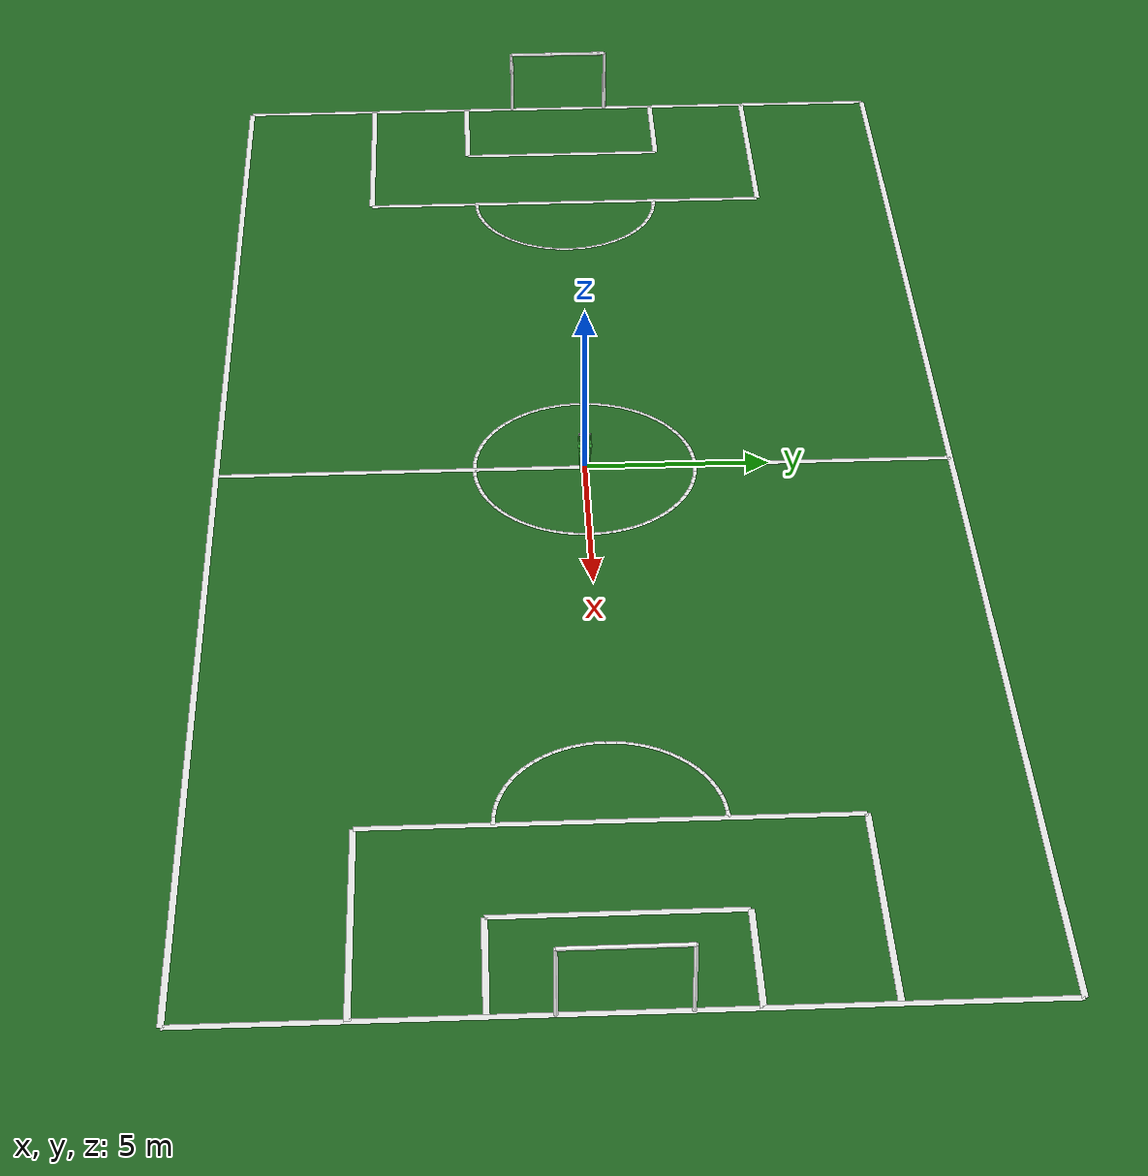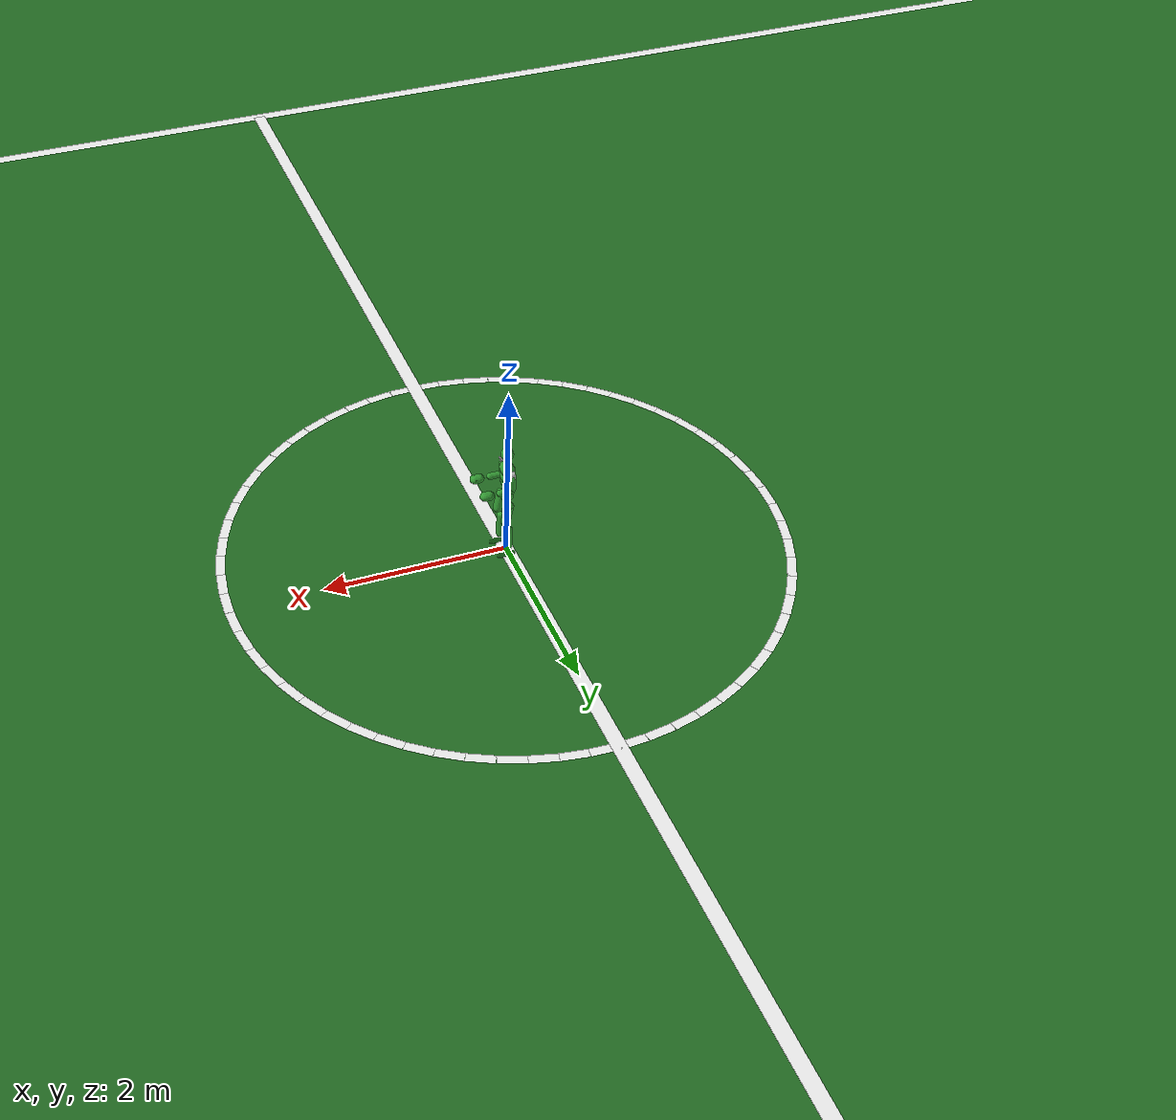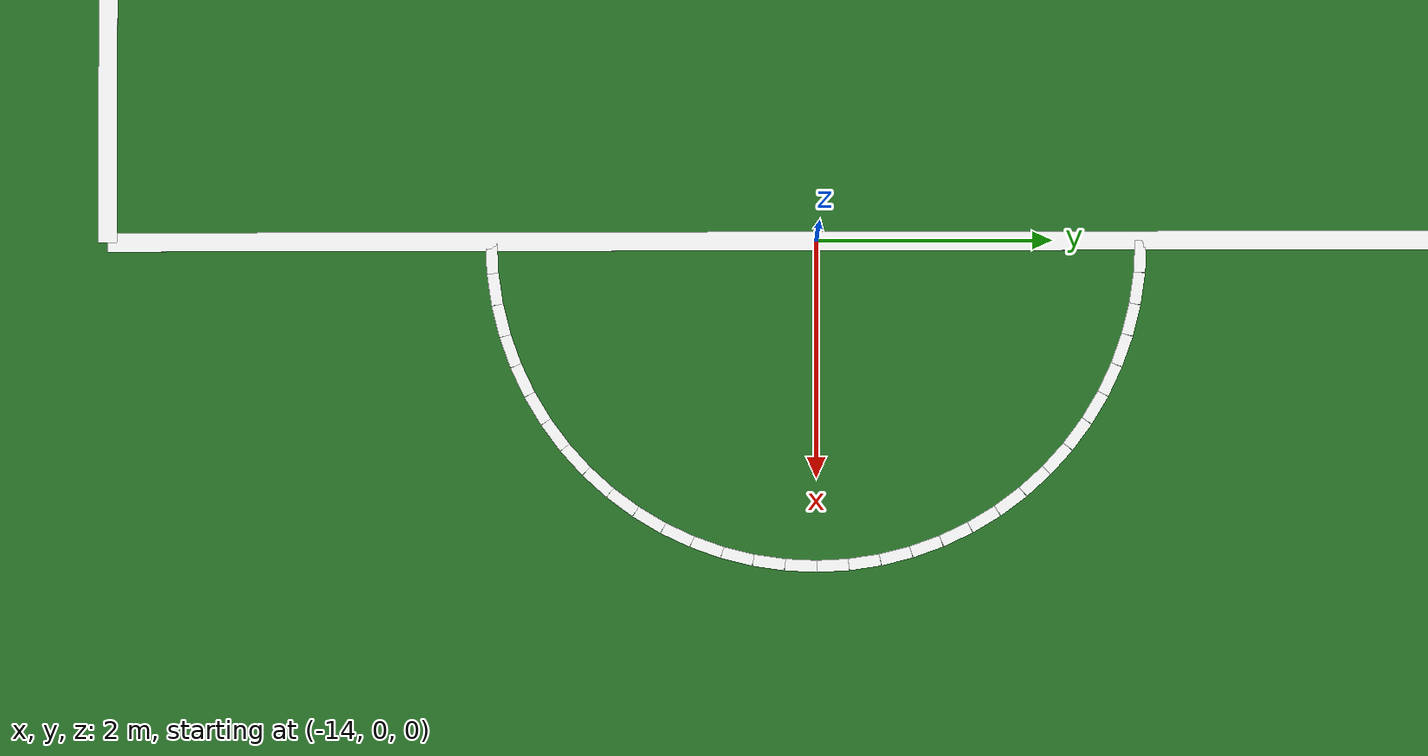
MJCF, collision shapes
<mujoco model="g1">
    <compiler angle="radian" meshdir="./meshes/"/>

    <default>
        <default class="g1">
            <geom contype="0" conaffinity="0"/>

            <!-- LocoMode/FSMDeploy 兼容：damping=0.001（与 g1_29dof_rev_1_0 一致），原 0.2 会导致动力学差异和左倾 -->
            <joint frictionloss="0.1" solimplimit="0.97 0.995 0.001" damping="0.001"/>

            <default class="hip">
                <default class="hip_pitch">
                    <joint axis="0 1 0" range="-2.5307 2.8798" actuatorfrcrange="-88 88" armature="0.01017752004"/>
                </default>
                <default class="hip_roll">
                    <joint axis="1 0 0" actuatorfrcrange="-139 139" armature="0.025101925"/>
                </default>
                <default class="hip_yaw">
                    <joint axis="0 0 1" range="-2.7576 2.7576" actuatorfrcrange="-88 88" armature="0.01017752004"/>
                </default>
            </default>
            <default class="knee">
                <joint axis="0 1 0" range="-0.087267 2.8798" actuatorfrcrange="-139 139" armature="0.025101925"/>
            </default>
            <default class="ankle">
                <default class="ankle_pitch">
                    <joint axis="0 1 0" range="-0.87267 0.5236" actuatorfrcrange="-50 50" armature="0.00721945"/>
                </default>
                <default class="ankle_roll">
                    <joint axis="1 0 0" range="-0.2618 0.2618" actuatorfrcrange="-50 50" armature="0.00721945"/>
                </default>
            </default>
            <default class="waist_yaw">
                <joint axis="0 0 1" range="-2.618 2.618" actuatorfrcrange="-88 88" armature="0.01017752004"/>
            </default>
            <default class="waist_pitch">
                <joint axis="0 1 0" range="-0.52 0.52" actuatorfrcrange="-50 50" armature="0.00721945"/>
            </default>
            <default class="waist_roll">
                <joint axis="1 0 0" range="-0.52 0.52" actuatorfrcrange="-50 50" armature="0.00721945"/>
            </default>
            <default class="shoulder">
                <default class="shoulder_pitch">
                    <joint axis="0 1 0" range="-3.0892 2.6704" actuatorfrcrange="-25 25" armature="0.003609725"/>
                </default>
                <default class="shoulder_roll">
                    <joint axis="1 0 0" actuatorfrcrange="-25 25" armature="0.003609725"/>
                </default>
                <default class="shoulder_yaw">
                    <joint axis="0 0 1" range="-2.618 2.618" actuatorfrcrange="-25 25" armature="0.003609725"/>
                </default>
            </default>
            <default class="elbow">
                <joint axis="0 1 0" range="-1.0472 2.0944" actuatorfrcrange="-25 25" armature="0.003609725"/>
            </default>
            <default class="wrist">
                <default class="wrist_roll">
                    <joint axis="1 0 0" range="-1.97222 1.97222" actuatorfrcrange="-25 25" armature="0.003609725"/>
                </default>
                <default class="wrist_pitch">
                    <joint axis="0 1 0" range="-1.61443 1.61443" actuatorfrcrange="-5 5" armature="0.00425"/>
                </default>
                <default class="wrist_yaw">
                    <joint axis="0 0 1" range="-1.61443 1.61443" actuatorfrcrange="-5 5" armature="0.00425"/>
                </default>
            </default>

            <default class="visual">
                <geom group="2" type="mesh" density="0" material="silver"/>
            </default>
            <default class="collision">
                <geom group="3" rgba=".2 .6 .2 .3" contype="1" conaffinity="1"/>
                <default class="foot">
                    <geom size="0.085 0.03 0.005"/>
                </default>
            </default>
            <site group="5" rgba="1 0 0 1"/>
        </default>
    </default>

    <asset>
        <material name="silver" rgba="0.7 0.7 0.7 1"/>
        <material name="black" rgba="0.2 0.2 0.2 1"/>

        <mesh name="pelvis" file="pelvis.STL"/>
        <mesh name="pelvis_contour_link" file="pelvis_contour_link.STL"/>
        <mesh name="left_hip_pitch_link" file="left_hip_pitch_link.STL"/>
        <mesh name="left_hip_roll_link" file="left_hip_roll_link.STL"/>
        <mesh name="left_hip_yaw_link" file="left_hip_yaw_link.STL"/>
        <mesh name="left_knee_link" file="left_knee_link.STL"/>
        <mesh name="left_ankle_pitch_link"
              file="left_ankle_pitch_link.STL"/>
        <mesh name="left_ankle_roll_link" file="left_ankle_roll_link.STL"/>
        <mesh name="right_hip_pitch_link" file="right_hip_pitch_link.STL"/>
        <mesh name="right_hip_roll_link" file="right_hip_roll_link.STL"/>
        <mesh name="right_hip_yaw_link" file="right_hip_yaw_link.STL"/>
        <mesh name="right_knee_link" file="right_knee_link.STL"/>
        <mesh name="right_ankle_pitch_link"
              file="right_ankle_pitch_link.STL"/>
        <mesh name="right_ankle_roll_link"
              file="right_ankle_roll_link.STL"/>
        <mesh name="waist_yaw_link" file="waist_yaw_link_rev_1_0.STL"/>
        <mesh name="waist_roll_link" file="waist_roll_link_rev_1_0.STL"/>
        <mesh name="torso_link" file="torso_link_rev_1_0.STL"/>
        <mesh name="logo_link" file="logo_link.STL"/>
        <mesh name="head_link" file="head_link.STL"/>
        <mesh name="left_shoulder_pitch_link"
              file="left_shoulder_pitch_link.STL"/>
        <mesh name="left_shoulder_roll_link"
              file="left_shoulder_roll_link.STL"/>
        <mesh name="left_shoulder_yaw_link"
              file="left_shoulder_yaw_link.STL"/>
        <mesh name="left_elbow_link" file="left_elbow_link.STL"/>
        <mesh name="left_wrist_roll_link" file="left_wrist_roll_link.STL"/>
        <mesh name="left_wrist_pitch_link"
              file="left_wrist_pitch_link.STL"/>
        <mesh name="left_wrist_yaw_link" file="left_wrist_yaw_link.STL"/>
        <mesh name="left_rubber_hand" file="left_rubber_hand.STL"/>
        <mesh name="right_shoulder_pitch_link"
              file="right_shoulder_pitch_link.STL"/>
        <mesh name="right_shoulder_roll_link"
              file="right_shoulder_roll_link.STL"/>
        <mesh name="right_shoulder_yaw_link"
              file="right_shoulder_yaw_link.STL"/>
        <mesh name="right_elbow_link" file="right_elbow_link.STL"/>
        <mesh name="right_wrist_roll_link"
              file="right_wrist_roll_link.STL"/>
        <mesh name="right_wrist_pitch_link"
              file="right_wrist_pitch_link.STL"/>
        <mesh name="right_wrist_yaw_link" file="right_wrist_yaw_link.STL"/>
        <mesh name="right_rubber_hand" file="right_rubber_hand.STL"/>

        <!-- 足球场天空 - 蓝色渐变 -->
        <texture type="skybox" builtin="flat" rgb1="0.5 0.7 1.0" rgb2="0.3 0.5 0.8" width="512" height="3072"/>
        <!-- 足球场草地纹理 - 纯绿色，使用flat texture确保颜色正确 -->
        <texture name="grass_texture" type="2d" builtin="flat" rgb1="0.15 0.45 0.15" rgb2="0.15 0.45 0.15" width="100" height="100"/>
        <material name="football_field" texture="grass_texture" texuniform="true" texrepeat="1 1" reflectance="0.1"/>
        <!-- 白色线条材质 - 用于足球场标记 -->
        <material name="field_line" rgba="1.0 1.0 1.0 1.0"/>
        <!-- 球门材质 - 白色 -->
        <material name="goal_post" rgba="1.0 1.0 1.0 1.0"/>

    </asset>

    <worldbody>
        <!-- 室外光照 - 模拟太阳光，更亮 -->
        <light name="key_light" directional="true" diffuse="1.0 1.0 0.95" specular="0.1 0.1 0.1"
               pos="10 10 15" dir="-0.5 -0.5 -1" castshadow="true" cutoff="255"/>
        <!-- 填充光 - 减少阴影 -->
        <light name="fill_light" directional="true" diffuse="0.7 0.7 0.7" specular="0.05 0.05 0.05"
               pos="-5 5 10" dir="0.3 -0.3 -1" castshadow="false" cutoff="255"/>
        <!-- 边缘光 - 增强轮廓 -->
        <light name="rim_light" directional="true" diffuse="0.4 0.4 0.4" specular="0.02 0.02 0.02"
               pos="0 -10 8" dir="0 0.5 -1" castshadow="false" cutoff="255"/>
        <!-- 环境光 - 模拟天空光 -->
        <light name="ambient_fill" directional="false" diffuse="0.5 0.6 0.7" specular="0 0 0"
               pos="0 0 10" castshadow="false" cutoff="255"/>
        <!-- 足球场地面 - 使用texture+material方式确保绿色显示，降低摩擦模拟草地 -->
        <geom name="football_field" size="0 0 0.05" friction="0.8 0.1 0.1" type="plane" material="football_field"/>

        <!-- ========== 5人制足球场标记 ========== -->
        <!-- 场地尺寸：长度40米（X方向：-20到20），宽度20米（Y方向：-10到10） -->
        <!-- 线条宽度：0.1米，无高度（贴在地面上） -->
        <!-- 注意：MuJoCo中box的size是半尺寸，cylinder的size是[radius, half-height] -->

        <!-- 边线和底线（外框）- 零碰撞，贴在地面上 -->
        <!-- 顶边线（Y=10米，沿X方向，长度40米） -->
        <geom name="top_line" type="box" size="20 0.08 0.0005" pos="0 10 0.0005" material="field_line" contype="0" conaffinity="0"/>
        <!-- 底边线（Y=-10米，沿X方向，长度40米） -->
        <geom name="bottom_line" type="box" size="20 0.08 0.0005" pos="0 -10 0.0005" material="field_line" contype="0" conaffinity="0"/>
        <!-- 左边线（X=-20米，沿Y方向，长度20米） -->
        <geom name="left_line" type="box" size="0.08 10 0.0005" pos="-20 0 0.0005" material="field_line" contype="0" conaffinity="0"/>
        <!-- 右边线（X=20米，沿Y方向，长度20米） -->
        <geom name="right_line" type="box" size="0.08 10 0.0005" pos="20 0 0.0005" material="field_line" contype="0" conaffinity="0"/>

        <!-- 中线（X=0米，沿Y方向，长度20米） -->
        <geom name="center_line" type="box" size="0.08 10 0.0005" pos="0 0 0.0005" material="field_line" contype="0" conaffinity="0"/>

        <!-- 中圈（半径3米，白色圆圈）- v3.29：64个点64条线，每5.625度一个点 -->
        <!-- 64个点64条线，每5.625度一个点 -->
        <!-- 线1：P1(0.00°)到P2(5.62°)，角度=92.81度=1.6199弧度，中点(2.9928,0.1470) -->
        <geom name="center_circle_line1" type="box" size="0.1472 0.05 0.0005" pos="2.9928 0.1470 0.0005" euler="0 0 1.6199" material="field_line" contype="0" conaffinity="0"/>
        <!-- 线2：P2(5.62°)到P3(11.25°)，角度=98.44度=1.7181弧度，中点(2.9640,0.4397) -->
        <geom name="center_circle_line2" type="box" size="0.1472 0.05 0.0005" pos="2.9640 0.4397 0.0005" euler="0 0 1.7181" material="field_line" contype="0" conaffinity="0"/>
        <!-- 线3：P3(11.25°)到P4(16.88°)，角度=104.06度=1.8162弧度，中点(2.9066,0.7281) -->
        <geom name="center_circle_line3" type="box" size="0.1472 0.05 0.0005" pos="2.9066 0.7281 0.0005" euler="0 0 1.8162" material="field_line" contype="0" conaffinity="0"/>
        <!-- 线4：P4(16.88°)到P5(22.50°)，角度=109.69度=1.9144弧度，中点(2.8212,1.0095) -->
        <geom name="center_circle_line4" type="box" size="0.1472 0.05 0.0005" pos="2.8212 1.0095 0.0005" euler="0 0 1.9144" material="field_line" contype="0" conaffinity="0"/>
        <!-- 线5：P5(22.50°)到P6(28.12°)，角度=115.31度=2.0126弧度，中点(2.7087,1.2811) -->
        <geom name="center_circle_line5" type="box" size="0.1472 0.05 0.0005" pos="2.7087 1.2811 0.0005" euler="0 0 2.0126" material="field_line" contype="0" conaffinity="0"/>
        <!-- 线6：P6(28.12°)到P7(33.75°)，角度=120.94度=2.1108弧度，中点(2.5701,1.5405) -->
        <geom name="center_circle_line6" type="box" size="0.1472 0.05 0.0005" pos="2.5701 1.5405 0.0005" euler="0 0 2.1108" material="field_line" contype="0" conaffinity="0"/>
        <!-- 线7：P7(33.75°)到P8(39.38°)，角度=126.56度=2.2089弧度，中点(2.4067,1.7849) -->
        <geom name="center_circle_line7" type="box" size="0.1472 0.05 0.0005" pos="2.4067 1.7849 0.0005" euler="0 0 2.2089" material="field_line" contype="0" conaffinity="0"/>
        <!-- 线8：P8(39.38°)到P9(45.00°)，角度=132.19度=2.3071弧度，中点(2.2202,2.0123) -->
        <geom name="center_circle_line8" type="box" size="0.1472 0.05 0.0005" pos="2.2202 2.0123 0.0005" euler="0 0 2.3071" material="field_line" contype="0" conaffinity="0"/>
        <!-- 线9：P9(45.00°)到P10(50.62°)，角度=137.81度=2.4053弧度，中点(2.0123,2.2202) -->
        <geom name="center_circle_line9" type="box" size="0.1472 0.05 0.0005" pos="2.0123 2.2202 0.0005" euler="0 0 2.4053" material="field_line" contype="0" conaffinity="0"/>
        <!-- 线10：P10(50.62°)到P11(56.25°)，角度=143.44度=2.5035弧度，中点(1.7849,2.4067) -->
        <geom name="center_circle_line10" type="box" size="0.1472 0.05 0.0005" pos="1.7849 2.4067 0.0005" euler="0 0 2.5035" material="field_line" contype="0" conaffinity="0"/>
        <!-- 线11：P11(56.25°)到P12(61.88°)，角度=149.06度=2.6016弧度，中点(1.5405,2.5701) -->
        <geom name="center_circle_line11" type="box" size="0.1472 0.05 0.0005" pos="1.5405 2.5701 0.0005" euler="0 0 2.6016" material="field_line" contype="0" conaffinity="0"/>
        <!-- 线12：P12(61.88°)到P13(67.50°)，角度=154.69度=2.6998弧度，中点(1.2811,2.7087) -->
        <geom name="center_circle_line12" type="box" size="0.1472 0.05 0.0005" pos="1.2811 2.7087 0.0005" euler="0 0 2.6998" material="field_line" contype="0" conaffinity="0"/>
        <!-- 线13：P13(67.50°)到P14(73.12°)，角度=160.31度=2.7980弧度，中点(1.0095,2.8212) -->
        <geom name="center_circle_line13" type="box" size="0.1472 0.05 0.0005" pos="1.0095 2.8212 0.0005" euler="0 0 2.7980" material="field_line" contype="0" conaffinity="0"/>
        <!-- 线14：P14(73.12°)到P15(78.75°)，角度=165.94度=2.8962弧度，中点(0.7281,2.9066) -->
        <geom name="center_circle_line14" type="box" size="0.1472 0.05 0.0005" pos="0.7281 2.9066 0.0005" euler="0 0 2.8962" material="field_line" contype="0" conaffinity="0"/>
        <!-- 线15：P15(78.75°)到P16(84.38°)，角度=171.56度=2.9943弧度，中点(0.4397,2.9640) -->
        <geom name="center_circle_line15" type="box" size="0.1472 0.05 0.0005" pos="0.4397 2.9640 0.0005" euler="0 0 2.9943" material="field_line" contype="0" conaffinity="0"/>
        <!-- 线16：P16(84.38°)到P17(90.00°)，角度=177.19度=3.0925弧度，中点(0.1470,2.9928) -->
        <geom name="center_circle_line16" type="box" size="0.1472 0.05 0.0005" pos="0.1470 2.9928 0.0005" euler="0 0 3.0925" material="field_line" contype="0" conaffinity="0"/>
        <!-- 线17：P17(90.00°)到P18(95.62°)，角度=182.81度=3.1907弧度，中点(-0.1470,2.9928) -->
        <geom name="center_circle_line17" type="box" size="0.1472 0.05 0.0005" pos="-0.1470 2.9928 0.0005" euler="0 0 3.1907" material="field_line" contype="0" conaffinity="0"/>
        <!-- 线18：P18(95.62°)到P19(101.25°)，角度=188.44度=3.2889弧度，中点(-0.4397,2.9640) -->
        <geom name="center_circle_line18" type="box" size="0.1472 0.05 0.0005" pos="-0.4397 2.9640 0.0005" euler="0 0 3.2889" material="field_line" contype="0" conaffinity="0"/>
        <!-- 线19：P19(101.25°)到P20(106.88°)，角度=194.06度=3.3870弧度，中点(-0.7281,2.9066) -->
        <geom name="center_circle_line19" type="box" size="0.1472 0.05 0.0005" pos="-0.7281 2.9066 0.0005" euler="0 0 3.3870" material="field_line" contype="0" conaffinity="0"/>
        <!-- 线20：P20(106.88°)到P21(112.50°)，角度=199.69度=3.4852弧度，中点(-1.0095,2.8212) -->
        <geom name="center_circle_line20" type="box" size="0.1472 0.05 0.0005" pos="-1.0095 2.8212 0.0005" euler="0 0 3.4852" material="field_line" contype="0" conaffinity="0"/>
        <!-- 线21：P21(112.50°)到P22(118.12°)，角度=205.31度=3.5834弧度，中点(-1.2811,2.7087) -->
        <geom name="center_circle_line21" type="box" size="0.1472 0.05 0.0005" pos="-1.2811 2.7087 0.0005" euler="0 0 3.5834" material="field_line" contype="0" conaffinity="0"/>
        <!-- 线22：P22(118.12°)到P23(123.75°)，角度=210.94度=3.6816弧度，中点(-1.5405,2.5701) -->
        <geom name="center_circle_line22" type="box" size="0.1472 0.05 0.0005" pos="-1.5405 2.5701 0.0005" euler="0 0 3.6816" material="field_line" contype="0" conaffinity="0"/>
        <!-- 线23：P23(123.75°)到P24(129.38°)，角度=216.56度=3.7797弧度，中点(-1.7849,2.4067) -->
        <geom name="center_circle_line23" type="box" size="0.1472 0.05 0.0005" pos="-1.7849 2.4067 0.0005" euler="0 0 3.7797" material="field_line" contype="0" conaffinity="0"/>
        <!-- 线24：P24(129.38°)到P25(135.00°)，角度=222.19度=3.8779弧度，中点(-2.0123,2.2202) -->
        <geom name="center_circle_line24" type="box" size="0.1472 0.05 0.0005" pos="-2.0123 2.2202 0.0005" euler="0 0 3.8779" material="field_line" contype="0" conaffinity="0"/>
        <!-- 线25：P25(135.00°)到P26(140.62°)，角度=227.81度=3.9761弧度，中点(-2.2202,2.0123) -->
        <geom name="center_circle_line25" type="box" size="0.1472 0.05 0.0005" pos="-2.2202 2.0123 0.0005" euler="0 0 3.9761" material="field_line" contype="0" conaffinity="0"/>
        <!-- 线26：P26(140.62°)到P27(146.25°)，角度=233.44度=4.0743弧度，中点(-2.4067,1.7849) -->
        <geom name="center_circle_line26" type="box" size="0.1472 0.05 0.0005" pos="-2.4067 1.7849 0.0005" euler="0 0 4.0743" material="field_line" contype="0" conaffinity="0"/>
        <!-- 线27：P27(146.25°)到P28(151.88°)，角度=239.06度=4.1724弧度，中点(-2.5701,1.5405) -->
        <geom name="center_circle_line27" type="box" size="0.1472 0.05 0.0005" pos="-2.5701 1.5405 0.0005" euler="0 0 4.1724" material="field_line" contype="0" conaffinity="0"/>
        <!-- 线28：P28(151.88°)到P29(157.50°)，角度=244.69度=4.2706弧度，中点(-2.7087,1.2811) -->
        <geom name="center_circle_line28" type="box" size="0.1472 0.05 0.0005" pos="-2.7087 1.2811 0.0005" euler="0 0 4.2706" material="field_line" contype="0" conaffinity="0"/>
        <!-- 线29：P29(157.50°)到P30(163.12°)，角度=250.31度=4.3688弧度，中点(-2.8212,1.0095) -->
        <geom name="center_circle_line29" type="box" size="0.1472 0.05 0.0005" pos="-2.8212 1.0095 0.0005" euler="0 0 4.3688" material="field_line" contype="0" conaffinity="0"/>
        <!-- 线30：P30(163.12°)到P31(168.75°)，角度=255.94度=4.4670弧度，中点(-2.9066,0.7281) -->
        <geom name="center_circle_line30" type="box" size="0.1472 0.05 0.0005" pos="-2.9066 0.7281 0.0005" euler="0 0 4.4670" material="field_line" contype="0" conaffinity="0"/>
        <!-- 线31：P31(168.75°)到P32(174.38°)，角度=261.56度=4.5651弧度，中点(-2.9640,0.4397) -->
        <geom name="center_circle_line31" type="box" size="0.1472 0.05 0.0005" pos="-2.9640 0.4397 0.0005" euler="0 0 4.5651" material="field_line" contype="0" conaffinity="0"/>
        <!-- 线32：P32(174.38°)到P33(180.00°)，角度=267.19度=4.6633弧度，中点(-2.9928,0.1470) -->
        <geom name="center_circle_line32" type="box" size="0.1472 0.05 0.0005" pos="-2.9928 0.1470 0.0005" euler="0 0 4.6633" material="field_line" contype="0" conaffinity="0"/>
        <!-- 线33：P33(180.00°)到P34(185.62°)，角度=272.81度=4.7615弧度，中点(-2.9928,-0.1470) -->
        <geom name="center_circle_line33" type="box" size="0.1472 0.05 0.0005" pos="-2.9928 -0.1470 0.0005" euler="0 0 4.7615" material="field_line" contype="0" conaffinity="0"/>
        <!-- 线34：P34(185.62°)到P35(191.25°)，角度=278.44度=4.8597弧度，中点(-2.9640,-0.4397) -->
        <geom name="center_circle_line34" type="box" size="0.1472 0.05 0.0005" pos="-2.9640 -0.4397 0.0005" euler="0 0 4.8597" material="field_line" contype="0" conaffinity="0"/>
        <!-- 线35：P35(191.25°)到P36(196.88°)，角度=284.06度=4.9578弧度，中点(-2.9066,-0.7281) -->
        <geom name="center_circle_line35" type="box" size="0.1472 0.05 0.0005" pos="-2.9066 -0.7281 0.0005" euler="0 0 4.9578" material="field_line" contype="0" conaffinity="0"/>
        <!-- 线36：P36(196.88°)到P37(202.50°)，角度=289.69度=5.0560弧度，中点(-2.8212,-1.0095) -->
        <geom name="center_circle_line36" type="box" size="0.1472 0.05 0.0005" pos="-2.8212 -1.0095 0.0005" euler="0 0 5.0560" material="field_line" contype="0" conaffinity="0"/>
        <!-- 线37：P37(202.50°)到P38(208.12°)，角度=295.31度=5.1542弧度，中点(-2.7087,-1.2811) -->
        <geom name="center_circle_line37" type="box" size="0.1472 0.05 0.0005" pos="-2.7087 -1.2811 0.0005" euler="0 0 5.1542" material="field_line" contype="0" conaffinity="0"/>
        <!-- 线38：P38(208.12°)到P39(213.75°)，角度=300.94度=5.2524弧度，中点(-2.5701,-1.5405) -->
        <geom name="center_circle_line38" type="box" size="0.1472 0.05 0.0005" pos="-2.5701 -1.5405 0.0005" euler="0 0 5.2524" material="field_line" contype="0" conaffinity="0"/>
        <!-- 线39：P39(213.75°)到P40(219.38°)，角度=306.56度=5.3505弧度，中点(-2.4067,-1.7849) -->
        <geom name="center_circle_line39" type="box" size="0.1472 0.05 0.0005" pos="-2.4067 -1.7849 0.0005" euler="0 0 5.3505" material="field_line" contype="0" conaffinity="0"/>
        <!-- 线40：P40(219.38°)到P41(225.00°)，角度=312.19度=5.4487弧度，中点(-2.2202,-2.0123) -->
        <geom name="center_circle_line40" type="box" size="0.1472 0.05 0.0005" pos="-2.2202 -2.0123 0.0005" euler="0 0 5.4487" material="field_line" contype="0" conaffinity="0"/>
        <!-- 线41：P41(225.00°)到P42(230.62°)，角度=317.81度=5.5469弧度，中点(-2.0123,-2.2202) -->
        <geom name="center_circle_line41" type="box" size="0.1472 0.05 0.0005" pos="-2.0123 -2.2202 0.0005" euler="0 0 5.5469" material="field_line" contype="0" conaffinity="0"/>
        <!-- 线42：P42(230.62°)到P43(236.25°)，角度=323.44度=5.6450弧度，中点(-1.7849,-2.4067) -->
        <geom name="center_circle_line42" type="box" size="0.1472 0.05 0.0005" pos="-1.7849 -2.4067 0.0005" euler="0 0 5.6450" material="field_line" contype="0" conaffinity="0"/>
        <!-- 线43：P43(236.25°)到P44(241.88°)，角度=329.06度=5.7432弧度，中点(-1.5405,-2.5701) -->
        <geom name="center_circle_line43" type="box" size="0.1472 0.05 0.0005" pos="-1.5405 -2.5701 0.0005" euler="0 0 5.7432" material="field_line" contype="0" conaffinity="0"/>
        <!-- 线44：P44(241.88°)到P45(247.50°)，角度=334.69度=5.8414弧度，中点(-1.2811,-2.7087) -->
        <geom name="center_circle_line44" type="box" size="0.1472 0.05 0.0005" pos="-1.2811 -2.7087 0.0005" euler="0 0 5.8414" material="field_line" contype="0" conaffinity="0"/>
        <!-- 线45：P45(247.50°)到P46(253.12°)，角度=340.31度=5.9396弧度，中点(-1.0095,-2.8212) -->
        <geom name="center_circle_line45" type="box" size="0.1472 0.05 0.0005" pos="-1.0095 -2.8212 0.0005" euler="0 0 5.9396" material="field_line" contype="0" conaffinity="0"/>
        <!-- 线46：P46(253.12°)到P47(258.75°)，角度=345.94度=6.0377弧度，中点(-0.7281,-2.9066) -->
        <geom name="center_circle_line46" type="box" size="0.1472 0.05 0.0005" pos="-0.7281 -2.9066 0.0005" euler="0 0 6.0377" material="field_line" contype="0" conaffinity="0"/>
        <!-- 线47：P47(258.75°)到P48(264.38°)，角度=351.56度=6.1359弧度，中点(-0.4397,-2.9640) -->
        <geom name="center_circle_line47" type="box" size="0.1472 0.05 0.0005" pos="-0.4397 -2.9640 0.0005" euler="0 0 6.1359" material="field_line" contype="0" conaffinity="0"/>
        <!-- 线48：P48(264.38°)到P49(270.00°)，角度=357.19度=6.2341弧度，中点(-0.1470,-2.9928) -->
        <geom name="center_circle_line48" type="box" size="0.1472 0.05 0.0005" pos="-0.1470 -2.9928 0.0005" euler="0 0 6.2341" material="field_line" contype="0" conaffinity="0"/>
        <!-- 线49：P49(270.00°)到P50(275.62°)，角度=2.81度=0.0491弧度，中点(0.1470,-2.9928) -->
        <geom name="center_circle_line49" type="box" size="0.1472 0.05 0.0005" pos="0.1470 -2.9928 0.0005" euler="0 0 0.0491" material="field_line" contype="0" conaffinity="0"/>
        <!-- 线50：P50(275.62°)到P51(281.25°)，角度=8.44度=0.1473弧度，中点(0.4397,-2.9640) -->
        <geom name="center_circle_line50" type="box" size="0.1472 0.05 0.0005" pos="0.4397 -2.9640 0.0005" euler="0 0 0.1473" material="field_line" contype="0" conaffinity="0"/>
        <!-- 线51：P51(281.25°)到P52(286.88°)，角度=14.06度=0.2454弧度，中点(0.7281,-2.9066) -->
        <geom name="center_circle_line51" type="box" size="0.1472 0.05 0.0005" pos="0.7281 -2.9066 0.0005" euler="0 0 0.2454" material="field_line" contype="0" conaffinity="0"/>
        <!-- 线52：P52(286.88°)到P53(292.50°)，角度=19.69度=0.3436弧度，中点(1.0095,-2.8212) -->
        <geom name="center_circle_line52" type="box" size="0.1472 0.05 0.0005" pos="1.0095 -2.8212 0.0005" euler="0 0 0.3436" material="field_line" contype="0" conaffinity="0"/>
        <!-- 线53：P53(292.50°)到P54(298.12°)，角度=25.31度=0.4418弧度，中点(1.2811,-2.7087) -->
        <geom name="center_circle_line53" type="box" size="0.1472 0.05 0.0005" pos="1.2811 -2.7087 0.0005" euler="0 0 0.4418" material="field_line" contype="0" conaffinity="0"/>
        <!-- 线54：P54(298.12°)到P55(303.75°)，角度=30.94度=0.5400弧度，中点(1.5405,-2.5701) -->
        <geom name="center_circle_line54" type="box" size="0.1472 0.05 0.0005" pos="1.5405 -2.5701 0.0005" euler="0 0 0.5400" material="field_line" contype="0" conaffinity="0"/>
        <!-- 线55：P55(303.75°)到P56(309.38°)，角度=36.56度=0.6381弧度，中点(1.7849,-2.4067) -->
        <geom name="center_circle_line55" type="box" size="0.1472 0.05 0.0005" pos="1.7849 -2.4067 0.0005" euler="0 0 0.6381" material="field_line" contype="0" conaffinity="0"/>
        <!-- 线56：P56(309.38°)到P57(315.00°)，角度=42.19度=0.7363弧度，中点(2.0123,-2.2202) -->
        <geom name="center_circle_line56" type="box" size="0.1472 0.05 0.0005" pos="2.0123 -2.2202 0.0005" euler="0 0 0.7363" material="field_line" contype="0" conaffinity="0"/>
        <!-- 线57：P57(315.00°)到P58(320.62°)，角度=47.81度=0.8345弧度，中点(2.2202,-2.0123) -->
        <geom name="center_circle_line57" type="box" size="0.1472 0.05 0.0005" pos="2.2202 -2.0123 0.0005" euler="0 0 0.8345" material="field_line" contype="0" conaffinity="0"/>
        <!-- 线58：P58(320.62°)到P59(326.25°)，角度=53.44度=0.9327弧度，中点(2.4067,-1.7849) -->
        <geom name="center_circle_line58" type="box" size="0.1472 0.05 0.0005" pos="2.4067 -1.7849 0.0005" euler="0 0 0.9327" material="field_line" contype="0" conaffinity="0"/>
        <!-- 线59：P59(326.25°)到P60(331.88°)，角度=59.06度=1.0308弧度，中点(2.5701,-1.5405) -->
        <geom name="center_circle_line59" type="box" size="0.1472 0.05 0.0005" pos="2.5701 -1.5405 0.0005" euler="0 0 1.0308" material="field_line" contype="0" conaffinity="0"/>
        <!-- 线60：P60(331.88°)到P61(337.50°)，角度=64.69度=1.1290弧度，中点(2.7087,-1.2811) -->
        <geom name="center_circle_line60" type="box" size="0.1472 0.05 0.0005" pos="2.7087 -1.2811 0.0005" euler="0 0 1.1290" material="field_line" contype="0" conaffinity="0"/>
        <!-- 线61：P61(337.50°)到P62(343.12°)，角度=70.31度=1.2272弧度，中点(2.8212,-1.0095) -->
        <geom name="center_circle_line61" type="box" size="0.1472 0.05 0.0005" pos="2.8212 -1.0095 0.0005" euler="0 0 1.2272" material="field_line" contype="0" conaffinity="0"/>
        <!-- 线62：P62(343.12°)到P63(348.75°)，角度=75.94度=1.3254弧度，中点(2.9066,-0.7281) -->
        <geom name="center_circle_line62" type="box" size="0.1472 0.05 0.0005" pos="2.9066 -0.7281 0.0005" euler="0 0 1.3254" material="field_line" contype="0" conaffinity="0"/>
        <!-- 线63：P63(348.75°)到P64(354.38°)，角度=81.56度=1.4235弧度，中点(2.9640,-0.4397) -->
        <geom name="center_circle_line63" type="box" size="0.1472 0.05 0.0005" pos="2.9640 -0.4397 0.0005" euler="0 0 1.4235" material="field_line" contype="0" conaffinity="0"/>
        <!-- 线64：P64(354.38°)到P1(0.00°)，角度=87.19度=1.5217弧度，中点(2.9928,-0.1470) -->
        <geom name="center_circle_line64" type="box" size="0.1472 0.05 0.0005" pos="2.9928 -0.1470 0.0005" euler="0 0 1.5217" material="field_line" contype="0" conaffinity="0"/>
                <!-- 左侧小禁区（矩形区域：从球门线X=-20米到小禁区线X=-17米，从Y=-3到Y=3米）- 零碰撞 -->
        <!-- 小禁区线（从Y=-3到Y=3米，X=-17米） -->
        <geom name="left_small_penalty_line" type="box" size="0.08 3 0.0005" pos="-17 0 0.0005" material="field_line" contype="0" conaffinity="0"/>
        <!-- 连接小禁区线和边线的顶边线（从X=-17到X=-20，Y=3米） -->
        <geom name="left_small_penalty_top" type="box" size="1.5 0.08 0.0005" pos="-18.5 3 0.0005" material="field_line" contype="0" conaffinity="0"/>
        <!-- 连接小禁区线和边线的底边线（从X=-17到X=-20，Y=-3米） -->
        <geom name="left_small_penalty_bottom" type="box" size="1.5 0.08 0.0005" pos="-18.5 -3 0.0005" material="field_line" contype="0" conaffinity="0"/>

        <!-- 左侧大禁区（矩形区域：从左边线X=-20米到禁区线X=-14米，从Y=-6到Y=6米）- 零碰撞 -->
        <!-- 禁区线（从Y=-6到Y=6米，X=-14米） -->
        <geom name="left_penalty_line" type="box" size="0.08 6 0.0005" pos="-14 0 0.0005" material="field_line" contype="0" conaffinity="0"/>
        <!-- 连接禁区线和边线的顶边线（从X=-14到X=-20，Y=6米） -->
        <geom name="left_penalty_top" type="box" size="3 0.08 0.0005" pos="-17 6 0.0005" material="field_line" contype="0" conaffinity="0"/>
        <!-- 连接禁区线和边线的底边线（从X=-14到X=-20，Y=-6米） -->
        <geom name="left_penalty_bottom" type="box" size="3 0.08 0.0005" pos="-17 -6 0.0005" material="field_line" contype="0" conaffinity="0"/>

        <!-- 左侧禁区弧顶（半径2.75米，直径5.5米，略小于小禁区宽度6米，中心在禁区线中点(-14,0)）- v3.32：32个点32条线 -->
        <!-- left弧线1：P1(-90.00°)到P2(-84.38°)，角度=2.81度=0.0491弧度，中点(-13.8652,-2.7434) -->
        <geom name="left_penalty_arc_line1" type="box" size="0.1349 0.05 0.0005" pos="-13.8652 -2.7434 0.0005" euler="0 0 0.0491" material="field_line" contype="0" conaffinity="0"/>
        <!-- left弧线2：P2(-84.38°)到P3(-78.75°)，角度=8.44度=0.1473弧度，中点(-13.5970,-2.7170) -->
        <geom name="left_penalty_arc_line2" type="box" size="0.1349 0.05 0.0005" pos="-13.5970 -2.7170 0.0005" euler="0 0 0.1473" material="field_line" contype="0" conaffinity="0"/>
        <!-- left弧线3：P3(-78.75°)到P4(-73.12°)，角度=14.06度=0.2454弧度，中点(-13.3326,-2.6644) -->
        <geom name="left_penalty_arc_line3" type="box" size="0.1349 0.05 0.0005" pos="-13.3326 -2.6644 0.0005" euler="0 0 0.2454" material="field_line" contype="0" conaffinity="0"/>
        <!-- left弧线4：P4(-73.12°)到P5(-67.50°)，角度=19.69度=0.3436弧度，中点(-13.0747,-2.5861) -->
        <geom name="left_penalty_arc_line4" type="box" size="0.1349 0.05 0.0005" pos="-13.0747 -2.5861 0.0005" euler="0 0 0.3436" material="field_line" contype="0" conaffinity="0"/>
        <!-- left弧线5：P5(-67.50°)到P6(-61.88°)，角度=25.31度=0.4418弧度，中点(-12.8256,-2.4830) -->
        <geom name="left_penalty_arc_line5" type="box" size="0.1349 0.05 0.0005" pos="-12.8256 -2.4830 0.0005" euler="0 0 0.4418" material="field_line" contype="0" conaffinity="0"/>
        <!-- left弧线6：P6(-61.88°)到P7(-56.25°)，角度=30.94度=0.5400弧度，中点(-12.5879,-2.3559) -->
        <geom name="left_penalty_arc_line6" type="box" size="0.1349 0.05 0.0005" pos="-12.5879 -2.3559 0.0005" euler="0 0 0.5400" material="field_line" contype="0" conaffinity="0"/>
        <!-- left弧线7：P7(-56.25°)到P8(-50.62°)，角度=36.56度=0.6381弧度，中点(-12.3638,-2.2062) -->
        <geom name="left_penalty_arc_line7" type="box" size="0.1349 0.05 0.0005" pos="-12.3638 -2.2062 0.0005" euler="0 0 0.6381" material="field_line" contype="0" conaffinity="0"/>
        <!-- left弧线8：P8(-50.62°)到P9(-45.00°)，角度=42.19度=0.7363弧度，中点(-12.1554,-2.0352) -->
        <geom name="left_penalty_arc_line8" type="box" size="0.1349 0.05 0.0005" pos="-12.1554 -2.0352 0.0005" euler="0 0 0.7363" material="field_line" contype="0" conaffinity="0"/>
        <!-- left弧线9：P9(-45.00°)到P10(-39.38°)，角度=47.81度=0.8345弧度，中点(-11.9648,-1.8446) -->
        <geom name="left_penalty_arc_line9" type="box" size="0.1349 0.05 0.0005" pos="-11.9648 -1.8446 0.0005" euler="0 0 0.8345" material="field_line" contype="0" conaffinity="0"/>
        <!-- left弧线10：P10(-39.38°)到P11(-33.75°)，角度=53.44度=0.9327弧度，中点(-11.7938,-1.6362) -->
        <geom name="left_penalty_arc_line10" type="box" size="0.1349 0.05 0.0005" pos="-11.7938 -1.6362 0.0005" euler="0 0 0.9327" material="field_line" contype="0" conaffinity="0"/>
        <!-- left弧线11：P11(-33.75°)到P12(-28.12°)，角度=59.06度=1.0308弧度，中点(-11.6441,-1.4121) -->
        <geom name="left_penalty_arc_line11" type="box" size="0.1349 0.05 0.0005" pos="-11.6441 -1.4121 0.0005" euler="0 0 1.0308" material="field_line" contype="0" conaffinity="0"/>
        <!-- left弧线12：P12(-28.12°)到P13(-22.50°)，角度=64.69度=1.1290弧度，中点(-11.5170,-1.1744) -->
        <geom name="left_penalty_arc_line12" type="box" size="0.1349 0.05 0.0005" pos="-11.5170 -1.1744 0.0005" euler="0 0 1.1290" material="field_line" contype="0" conaffinity="0"/>
        <!-- left弧线13：P13(-22.50°)到P14(-16.88°)，角度=70.31度=1.2272弧度，中点(-11.4139,-0.9253) -->
        <geom name="left_penalty_arc_line13" type="box" size="0.1349 0.05 0.0005" pos="-11.4139 -0.9253 0.0005" euler="0 0 1.2272" material="field_line" contype="0" conaffinity="0"/>
        <!-- left弧线14：P14(-16.88°)到P15(-11.25°)，角度=75.94度=1.3254弧度，中点(-11.3356,-0.6674) -->
        <geom name="left_penalty_arc_line14" type="box" size="0.1349 0.05 0.0005" pos="-11.3356 -0.6674 0.0005" euler="0 0 1.3254" material="field_line" contype="0" conaffinity="0"/>
        <!-- left弧线15：P15(-11.25°)到P16(-5.62°)，角度=81.56度=1.4235弧度，中点(-11.2830,-0.4030) -->
        <geom name="left_penalty_arc_line15" type="box" size="0.1349 0.05 0.0005" pos="-11.2830 -0.4030 0.0005" euler="0 0 1.4235" material="field_line" contype="0" conaffinity="0"/>
        <!-- left弧线16：P16(-5.62°)到P17(0.00°)，角度=87.19度=1.5217弧度，中点(-11.2566,-0.1348) -->
        <geom name="left_penalty_arc_line16" type="box" size="0.1349 0.05 0.0005" pos="-11.2566 -0.1348 0.0005" euler="0 0 1.5217" material="field_line" contype="0" conaffinity="0"/>
        <!-- left弧线17：P17(0.00°)到P18(5.62°)，角度=92.81度=1.6199弧度，中点(-11.2566,0.1348) -->
        <geom name="left_penalty_arc_line17" type="box" size="0.1349 0.05 0.0005" pos="-11.2566 0.1348 0.0005" euler="0 0 1.6199" material="field_line" contype="0" conaffinity="0"/>
        <!-- left弧线18：P18(5.62°)到P19(11.25°)，角度=98.44度=1.7181弧度，中点(-11.2830,0.4030) -->
        <geom name="left_penalty_arc_line18" type="box" size="0.1349 0.05 0.0005" pos="-11.2830 0.4030 0.0005" euler="0 0 1.7181" material="field_line" contype="0" conaffinity="0"/>
        <!-- left弧线19：P19(11.25°)到P20(16.88°)，角度=104.06度=1.8162弧度，中点(-11.3356,0.6674) -->
        <geom name="left_penalty_arc_line19" type="box" size="0.1349 0.05 0.0005" pos="-11.3356 0.6674 0.0005" euler="0 0 1.8162" material="field_line" contype="0" conaffinity="0"/>
        <!-- left弧线20：P20(16.88°)到P21(22.50°)，角度=109.69度=1.9144弧度，中点(-11.4139,0.9253) -->
        <geom name="left_penalty_arc_line20" type="box" size="0.1349 0.05 0.0005" pos="-11.4139 0.9253 0.0005" euler="0 0 1.9144" material="field_line" contype="0" conaffinity="0"/>
        <!-- left弧线21：P21(22.50°)到P22(28.12°)，角度=115.31度=2.0126弧度，中点(-11.5170,1.1744) -->
        <geom name="left_penalty_arc_line21" type="box" size="0.1349 0.05 0.0005" pos="-11.5170 1.1744 0.0005" euler="0 0 2.0126" material="field_line" contype="0" conaffinity="0"/>
        <!-- left弧线22：P22(28.12°)到P23(33.75°)，角度=120.94度=2.1108弧度，中点(-11.6441,1.4121) -->
        <geom name="left_penalty_arc_line22" type="box" size="0.1349 0.05 0.0005" pos="-11.6441 1.4121 0.0005" euler="0 0 2.1108" material="field_line" contype="0" conaffinity="0"/>
        <!-- left弧线23：P23(33.75°)到P24(39.38°)，角度=126.56度=2.2089弧度，中点(-11.7938,1.6362) -->
        <geom name="left_penalty_arc_line23" type="box" size="0.1349 0.05 0.0005" pos="-11.7938 1.6362 0.0005" euler="0 0 2.2089" material="field_line" contype="0" conaffinity="0"/>
        <!-- left弧线24：P24(39.38°)到P25(45.00°)，角度=132.19度=2.3071弧度，中点(-11.9648,1.8446) -->
        <geom name="left_penalty_arc_line24" type="box" size="0.1349 0.05 0.0005" pos="-11.9648 1.8446 0.0005" euler="0 0 2.3071" material="field_line" contype="0" conaffinity="0"/>
        <!-- left弧线25：P25(45.00°)到P26(50.62°)，角度=137.81度=2.4053弧度，中点(-12.1554,2.0352) -->
        <geom name="left_penalty_arc_line25" type="box" size="0.1349 0.05 0.0005" pos="-12.1554 2.0352 0.0005" euler="0 0 2.4053" material="field_line" contype="0" conaffinity="0"/>
        <!-- left弧线26：P26(50.62°)到P27(56.25°)，角度=143.44度=2.5035弧度，中点(-12.3638,2.2062) -->
        <geom name="left_penalty_arc_line26" type="box" size="0.1349 0.05 0.0005" pos="-12.3638 2.2062 0.0005" euler="0 0 2.5035" material="field_line" contype="0" conaffinity="0"/>
        <!-- left弧线27：P27(56.25°)到P28(61.88°)，角度=149.06度=2.6016弧度，中点(-12.5879,2.3559) -->
        <geom name="left_penalty_arc_line27" type="box" size="0.1349 0.05 0.0005" pos="-12.5879 2.3559 0.0005" euler="0 0 2.6016" material="field_line" contype="0" conaffinity="0"/>
        <!-- left弧线28：P28(61.88°)到P29(67.50°)，角度=154.69度=2.6998弧度，中点(-12.8256,2.4830) -->
        <geom name="left_penalty_arc_line28" type="box" size="0.1349 0.05 0.0005" pos="-12.8256 2.4830 0.0005" euler="0 0 2.6998" material="field_line" contype="0" conaffinity="0"/>
        <!-- left弧线29：P29(67.50°)到P30(73.12°)，角度=160.31度=2.7980弧度，中点(-13.0747,2.5861) -->
        <geom name="left_penalty_arc_line29" type="box" size="0.1349 0.05 0.0005" pos="-13.0747 2.5861 0.0005" euler="0 0 2.7980" material="field_line" contype="0" conaffinity="0"/>
        <!-- left弧线30：P30(73.12°)到P31(78.75°)，角度=165.94度=2.8962弧度，中点(-13.3326,2.6644) -->
        <geom name="left_penalty_arc_line30" type="box" size="0.1349 0.05 0.0005" pos="-13.3326 2.6644 0.0005" euler="0 0 2.8962" material="field_line" contype="0" conaffinity="0"/>
        <!-- left弧线31：P31(78.75°)到P32(84.38°)，角度=171.56度=2.9943弧度，中点(-13.5970,2.7170) -->
        <geom name="left_penalty_arc_line31" type="box" size="0.1349 0.05 0.0005" pos="-13.5970 2.7170 0.0005" euler="0 0 2.9943" material="field_line" contype="0" conaffinity="0"/>
        <!-- left弧线32：P32(84.38°)到P33(90.00°)，角度=177.19度=3.0925弧度，中点(-13.8652,2.7434) -->
        <geom name="left_penalty_arc_line32" type="box" size="0.1349 0.05 0.0005" pos="-13.8652 2.7434 0.0005" euler="0 0 3.0925" material="field_line" contype="0" conaffinity="0"/>

                <!-- 右侧禁区弧顶（半径2.75米，直径5.5米，略小于小禁区宽度6米，中心在禁区线中点(14,0)）- v3.32：32个点32条线 -->
        <!-- right弧线1：P1(90.00°)到P2(95.62°)，角度=182.81度=3.1907弧度，中点(13.8652,2.7434) -->
        <geom name="right_penalty_arc_line1" type="box" size="0.1349 0.05 0.0005" pos="13.8652 2.7434 0.0005" euler="0 0 3.1907" material="field_line" contype="0" conaffinity="0"/>
        <!-- right弧线2：P2(95.62°)到P3(101.25°)，角度=188.44度=3.2889弧度，中点(13.5970,2.7170) -->
        <geom name="right_penalty_arc_line2" type="box" size="0.1349 0.05 0.0005" pos="13.5970 2.7170 0.0005" euler="0 0 3.2889" material="field_line" contype="0" conaffinity="0"/>
        <!-- right弧线3：P3(101.25°)到P4(106.88°)，角度=194.06度=3.3870弧度，中点(13.3326,2.6644) -->
        <geom name="right_penalty_arc_line3" type="box" size="0.1349 0.05 0.0005" pos="13.3326 2.6644 0.0005" euler="0 0 3.3870" material="field_line" contype="0" conaffinity="0"/>
        <!-- right弧线4：P4(106.88°)到P5(112.50°)，角度=199.69度=3.4852弧度，中点(13.0747,2.5861) -->
        <geom name="right_penalty_arc_line4" type="box" size="0.1349 0.05 0.0005" pos="13.0747 2.5861 0.0005" euler="0 0 3.4852" material="field_line" contype="0" conaffinity="0"/>
        <!-- right弧线5：P5(112.50°)到P6(118.12°)，角度=205.31度=3.5834弧度，中点(12.8256,2.4830) -->
        <geom name="right_penalty_arc_line5" type="box" size="0.1349 0.05 0.0005" pos="12.8256 2.4830 0.0005" euler="0 0 3.5834" material="field_line" contype="0" conaffinity="0"/>
        <!-- right弧线6：P6(118.12°)到P7(123.75°)，角度=210.94度=3.6816弧度，中点(12.5879,2.3559) -->
        <geom name="right_penalty_arc_line6" type="box" size="0.1349 0.05 0.0005" pos="12.5879 2.3559 0.0005" euler="0 0 3.6816" material="field_line" contype="0" conaffinity="0"/>
        <!-- right弧线7：P7(123.75°)到P8(129.38°)，角度=216.56度=3.7797弧度，中点(12.3638,2.2062) -->
        <geom name="right_penalty_arc_line7" type="box" size="0.1349 0.05 0.0005" pos="12.3638 2.2062 0.0005" euler="0 0 3.7797" material="field_line" contype="0" conaffinity="0"/>
        <!-- right弧线8：P8(129.38°)到P9(135.00°)，角度=222.19度=3.8779弧度，中点(12.1554,2.0352) -->
        <geom name="right_penalty_arc_line8" type="box" size="0.1349 0.05 0.0005" pos="12.1554 2.0352 0.0005" euler="0 0 3.8779" material="field_line" contype="0" conaffinity="0"/>
        <!-- right弧线9：P9(135.00°)到P10(140.62°)，角度=227.81度=3.9761弧度，中点(11.9648,1.8446) -->
        <geom name="right_penalty_arc_line9" type="box" size="0.1349 0.05 0.0005" pos="11.9648 1.8446 0.0005" euler="0 0 3.9761" material="field_line" contype="0" conaffinity="0"/>
        <!-- right弧线10：P10(140.62°)到P11(146.25°)，角度=233.44度=4.0743弧度，中点(11.7938,1.6362) -->
        <geom name="right_penalty_arc_line10" type="box" size="0.1349 0.05 0.0005" pos="11.7938 1.6362 0.0005" euler="0 0 4.0743" material="field_line" contype="0" conaffinity="0"/>
        <!-- right弧线11：P11(146.25°)到P12(151.88°)，角度=239.06度=4.1724弧度，中点(11.6441,1.4121) -->
        <geom name="right_penalty_arc_line11" type="box" size="0.1349 0.05 0.0005" pos="11.6441 1.4121 0.0005" euler="0 0 4.1724" material="field_line" contype="0" conaffinity="0"/>
        <!-- right弧线12：P12(151.88°)到P13(157.50°)，角度=244.69度=4.2706弧度，中点(11.5170,1.1744) -->
        <geom name="right_penalty_arc_line12" type="box" size="0.1349 0.05 0.0005" pos="11.5170 1.1744 0.0005" euler="0 0 4.2706" material="field_line" contype="0" conaffinity="0"/>
        <!-- right弧线13：P13(157.50°)到P14(163.12°)，角度=250.31度=4.3688弧度，中点(11.4139,0.9253) -->
        <geom name="right_penalty_arc_line13" type="box" size="0.1349 0.05 0.0005" pos="11.4139 0.9253 0.0005" euler="0 0 4.3688" material="field_line" contype="0" conaffinity="0"/>
        <!-- right弧线14：P14(163.12°)到P15(168.75°)，角度=255.94度=4.4670弧度，中点(11.3356,0.6674) -->
        <geom name="right_penalty_arc_line14" type="box" size="0.1349 0.05 0.0005" pos="11.3356 0.6674 0.0005" euler="0 0 4.4670" material="field_line" contype="0" conaffinity="0"/>
        <!-- right弧线15：P15(168.75°)到P16(174.38°)，角度=261.56度=4.5651弧度，中点(11.2830,0.4030) -->
        <geom name="right_penalty_arc_line15" type="box" size="0.1349 0.05 0.0005" pos="11.2830 0.4030 0.0005" euler="0 0 4.5651" material="field_line" contype="0" conaffinity="0"/>
        <!-- right弧线16：P16(174.38°)到P17(180.00°)，角度=267.19度=4.6633弧度，中点(11.2566,0.1348) -->
        <geom name="right_penalty_arc_line16" type="box" size="0.1349 0.05 0.0005" pos="11.2566 0.1348 0.0005" euler="0 0 4.6633" material="field_line" contype="0" conaffinity="0"/>
        <!-- right弧线17：P17(180.00°)到P18(185.62°)，角度=272.81度=4.7615弧度，中点(11.2566,-0.1348) -->
        <geom name="right_penalty_arc_line17" type="box" size="0.1349 0.05 0.0005" pos="11.2566 -0.1348 0.0005" euler="0 0 4.7615" material="field_line" contype="0" conaffinity="0"/>
        <!-- right弧线18：P18(185.62°)到P19(191.25°)，角度=278.44度=4.8597弧度，中点(11.2830,-0.4030) -->
        <geom name="right_penalty_arc_line18" type="box" size="0.1349 0.05 0.0005" pos="11.2830 -0.4030 0.0005" euler="0 0 4.8597" material="field_line" contype="0" conaffinity="0"/>
        <!-- right弧线19：P19(191.25°)到P20(196.88°)，角度=284.06度=4.9578弧度，中点(11.3356,-0.6674) -->
        <geom name="right_penalty_arc_line19" type="box" size="0.1349 0.05 0.0005" pos="11.3356 -0.6674 0.0005" euler="0 0 4.9578" material="field_line" contype="0" conaffinity="0"/>
        <!-- right弧线20：P20(196.88°)到P21(202.50°)，角度=289.69度=5.0560弧度，中点(11.4139,-0.9253) -->
        <geom name="right_penalty_arc_line20" type="box" size="0.1349 0.05 0.0005" pos="11.4139 -0.9253 0.0005" euler="0 0 5.0560" material="field_line" contype="0" conaffinity="0"/>
        <!-- right弧线21：P21(202.50°)到P22(208.12°)，角度=295.31度=5.1542弧度，中点(11.5170,-1.1744) -->
        <geom name="right_penalty_arc_line21" type="box" size="0.1349 0.05 0.0005" pos="11.5170 -1.1744 0.0005" euler="0 0 5.1542" material="field_line" contype="0" conaffinity="0"/>
        <!-- right弧线22：P22(208.12°)到P23(213.75°)，角度=300.94度=5.2524弧度，中点(11.6441,-1.4121) -->
        <geom name="right_penalty_arc_line22" type="box" size="0.1349 0.05 0.0005" pos="11.6441 -1.4121 0.0005" euler="0 0 5.2524" material="field_line" contype="0" conaffinity="0"/>
        <!-- right弧线23：P23(213.75°)到P24(219.38°)，角度=306.56度=5.3505弧度，中点(11.7938,-1.6362) -->
        <geom name="right_penalty_arc_line23" type="box" size="0.1349 0.05 0.0005" pos="11.7938 -1.6362 0.0005" euler="0 0 5.3505" material="field_line" contype="0" conaffinity="0"/>
        <!-- right弧线24：P24(219.38°)到P25(225.00°)，角度=312.19度=5.4487弧度，中点(11.9648,-1.8446) -->
        <geom name="right_penalty_arc_line24" type="box" size="0.1349 0.05 0.0005" pos="11.9648 -1.8446 0.0005" euler="0 0 5.4487" material="field_line" contype="0" conaffinity="0"/>
        <!-- right弧线25：P25(225.00°)到P26(230.62°)，角度=317.81度=5.5469弧度，中点(12.1554,-2.0352) -->
        <geom name="right_penalty_arc_line25" type="box" size="0.1349 0.05 0.0005" pos="12.1554 -2.0352 0.0005" euler="0 0 5.5469" material="field_line" contype="0" conaffinity="0"/>
        <!-- right弧线26：P26(230.62°)到P27(236.25°)，角度=323.44度=5.6450弧度，中点(12.3638,-2.2062) -->
        <geom name="right_penalty_arc_line26" type="box" size="0.1349 0.05 0.0005" pos="12.3638 -2.2062 0.0005" euler="0 0 5.6450" material="field_line" contype="0" conaffinity="0"/>
        <!-- right弧线27：P27(236.25°)到P28(241.88°)，角度=329.06度=5.7432弧度，中点(12.5879,-2.3559) -->
        <geom name="right_penalty_arc_line27" type="box" size="0.1349 0.05 0.0005" pos="12.5879 -2.3559 0.0005" euler="0 0 5.7432" material="field_line" contype="0" conaffinity="0"/>
        <!-- right弧线28：P28(241.88°)到P29(247.50°)，角度=334.69度=5.8414弧度，中点(12.8256,-2.4830) -->
        <geom name="right_penalty_arc_line28" type="box" size="0.1349 0.05 0.0005" pos="12.8256 -2.4830 0.0005" euler="0 0 5.8414" material="field_line" contype="0" conaffinity="0"/>
        <!-- right弧线29：P29(247.50°)到P30(253.12°)，角度=340.31度=5.9396弧度，中点(13.0747,-2.5861) -->
        <geom name="right_penalty_arc_line29" type="box" size="0.1349 0.05 0.0005" pos="13.0747 -2.5861 0.0005" euler="0 0 5.9396" material="field_line" contype="0" conaffinity="0"/>
        <!-- right弧线30：P30(253.12°)到P31(258.75°)，角度=345.94度=6.0377弧度，中点(13.3326,-2.6644) -->
        <geom name="right_penalty_arc_line30" type="box" size="0.1349 0.05 0.0005" pos="13.3326 -2.6644 0.0005" euler="0 0 6.0377" material="field_line" contype="0" conaffinity="0"/>
        <!-- right弧线31：P31(258.75°)到P32(264.38°)，角度=351.56度=6.1359弧度，中点(13.5970,-2.7170) -->
        <geom name="right_penalty_arc_line31" type="box" size="0.1349 0.05 0.0005" pos="13.5970 -2.7170 0.0005" euler="0 0 6.1359" material="field_line" contype="0" conaffinity="0"/>
        <!-- right弧线32：P32(264.38°)到P33(270.00°)，角度=357.19度=6.2341弧度，中点(13.8652,-2.7434) -->
        <geom name="right_penalty_arc_line32" type="box" size="0.1349 0.05 0.0005" pos="13.8652 -2.7434 0.0005" euler="0 0 6.2341" material="field_line" contype="0" conaffinity="0"/>

        <!-- 右侧小禁区（矩形区域：从球门线X=20米到小禁区线X=17米，从Y=-3到Y=3米）- 零碰撞 - v3.33 -->
        <!-- 小禁区线（从Y=-3到Y=3米，X=17米） -->
        <geom name="right_small_penalty_line" type="box" size="0.08 3 0.0005" pos="17 0 0.0005" material="field_line" contype="0" conaffinity="0"/>
        <!-- 连接小禁区线和边线的顶边线（从X=17到X=20，Y=3米） -->
        <geom name="right_small_penalty_top" type="box" size="1.5 0.08 0.0005" pos="18.5 3 0.0005" material="field_line" contype="0" conaffinity="0"/>
        <!-- 连接小禁区线和边线的底边线（从X=17到X=20，Y=-3米） -->
        <geom name="right_small_penalty_bottom" type="box" size="1.5 0.08 0.0005" pos="18.5 -3 0.0005" material="field_line" contype="0" conaffinity="0"/>

        <!-- 右侧大禁区（矩形区域：从右边线X=20米到禁区线X=14米，从Y=-6到Y=6米）- 零碰撞 - v3.33 -->
        <!-- 禁区线（从Y=-6到Y=6米，X=14米） -->
        <geom name="right_penalty_line" type="box" size="0.08 6 0.0005" pos="14 0 0.0005" material="field_line" contype="0" conaffinity="0"/>
        <!-- 连接禁区线和边线的顶边线（从X=14到X=20，Y=6米） -->
        <geom name="right_penalty_top" type="box" size="3 0.08 0.0005" pos="17 6 0.0005" material="field_line" contype="0" conaffinity="0"/>
        <!-- 连接禁区线和边线的底边线（从X=14到X=20，Y=-6米） -->
        <geom name="right_penalty_bottom" type="box" size="3 0.08 0.0005" pos="17 -6 0.0005" material="field_line" contype="0" conaffinity="0"/>
                <!-- 左侧球门（X=-20米，球门宽3米，高2米） -->
        <body name="left_goal" pos="-20 0 0">
            <!-- 左立柱（垂直，高度2米，半径0.05米） -->
            <geom name="left_goal_post_left" type="cylinder" size="0.05 1" pos="0 1.5 1" material="goal_post"/>
            <!-- 右立柱（垂直，高度2米，半径0.05米） -->
            <geom name="left_goal_post_right" type="cylinder" size="0.05 1" pos="0 -1.5 1" material="goal_post"/>
            <!-- 横梁（水平，长度3米，半径0.05米，旋转90度绕X轴） -->
            <geom name="left_goal_crossbar" type="cylinder" size="0.05 1.5" pos="0 0 2" quat="0.707107 0.707107 0 0" material="goal_post"/>
        </body>

        <!-- 右侧球门（X=20米，球门宽3米，高2米） -->
        <body name="right_goal" pos="20 0 0">
            <!-- 左立柱（垂直，高度2米，半径0.05米） -->
            <geom name="right_goal_post_left" type="cylinder" size="0.05 1" pos="0 1.5 1" material="goal_post"/>
            <!-- 右立柱（垂直，高度2米，半径0.05米） -->
            <geom name="right_goal_post_right" type="cylinder" size="0.05 1" pos="0 -1.5 1" material="goal_post"/>
            <!-- 横梁（水平，长度3米，半径0.05米，旋转90度绕X轴） -->
            <geom name="right_goal_crossbar" type="cylinder" size="0.05 1.5" pos="0 0 2" quat="0.707107 0.707107 0 0" material="goal_post"/>
        </body>
        <!-- ========== 足球场标记结束 ========== -->

        <body name="pelvis" pos="0 0 0.8" childclass="g1">
            <inertial pos="0 0 -0.07605" quat="1 0 -0.000399148 0" mass="3.813" diaginertia="0.010549 0.0093089 0.0079184"/>
            <freejoint name="floating_base_joint"/>
            <geom class="visual" material="black" mesh="pelvis"/>
            <geom class="visual" mesh="pelvis_contour_link"/>
            <geom mesh="pelvis_contour_link" class="visual"/>
            <geom name="pelvis_collision" class="collision" type="sphere" size="0.07" pos="0 0 -0.08"/>
            <site name="imu_in_pelvis" size="0.01" pos="0.04525 0 -0.08339"/>
            <site name="pelvis" size="0.01" pos="0 0 0"/>
            <body name="left_hip_pitch_link" pos="0 0.064452 -0.1027">
                <inertial pos="0.002741 0.047791 -0.02606" quat="0.954862 0.293964 0.0302556 0.030122" mass="1.35"
                          diaginertia="0.00181517 0.00153422 0.00116212"/>
                <joint name="left_hip_pitch_joint" class="hip_pitch"/>
                <geom class="visual" material="black" mesh="left_hip_pitch_link"/>
                <geom material="black" mesh="left_hip_pitch_link" class="visual"/>
                <body name="left_hip_roll_link" pos="0 0.052 -0.030465" quat="0.996179 0 -0.0873386 0">
                    <inertial pos="0.029812 -0.001045 -0.087934" quat="0.977808 -1.97119e-05 0.205576 -0.0403793" mass="1.52"
                              diaginertia="0.00254986 0.00241169 0.00148755"/>
                    <joint name="left_hip_roll_joint" class="hip_roll" range="-0.5236 2.9671"/>
                    <geom class="visual" mesh="left_hip_roll_link"/>
                    <geom mesh="left_hip_roll_link" class="visual"/>
                    <geom name="left_thigh" class="collision" type="capsule" size="0.05" fromto="0.02 0 0 0.02 0 -0.2"/>
                    <body name="left_hip_yaw_link" pos="0.025001 0 -0.12412">
                        <inertial pos="-0.057709 -0.010981 -0.15078" quat="0.600598 0.15832 0.223482 0.751181" mass="1.702"
                                  diaginertia="0.00776166 0.00717575 0.00160139"/>
                        <joint name="left_hip_yaw_joint" class="hip_yaw"/>
                        <geom class="visual" mesh="left_hip_yaw_link"/>
                        <body name="left_knee_link" pos="-0.078273 0.0021489 -0.17734" quat="0.996179 0 0.0873386 0">
                            <inertial pos="0.005457 0.003964 -0.12074" quat="0.923418 -0.0327699 0.0158246 0.382067" mass="1.932"
                                      diaginertia="0.0113804 0.0112778 0.00146458"/>
                            <joint name="left_knee_joint" class="knee"/>
                            <geom class="visual" mesh="left_knee_link"/>
                            <geom name="left_shin" class="collision" type="capsule" size="0.04" fromto="0.02 0 0 0.02 0 -0.25"/>
                            <body name="left_ankle_pitch_link" pos="0 -9.4445e-05 -0.30001">
                                <inertial pos="-0.007269 0 0.011137" quat="0.603053 0.369225 0.369225 0.603053" mass="0.074"
                                          diaginertia="1.89e-05 1.40805e-05 6.9195e-06"/>
                                <joint name="left_ankle_pitch_joint" class="ankle_pitch"/>
                                <geom class="visual" mesh="left_ankle_pitch_link"/>
                                <body name="left_ankle_roll_link" pos="0 0 -0.017558">
                                    <site name="left_foot" rgba="1 0 0 1"/>
                                    <inertial pos="0.026505 0 -0.016425" quat="-0.000481092 0.728482 -0.000618967 0.685065" mass="0.608"
                                              diaginertia="0.00167218 0.0016161 0.000217621"/>
                                    <joint name="left_ankle_roll_joint" class="ankle_roll"/>
                                    <geom class="visual" material="black" mesh="left_ankle_roll_link"/>
                                    <geom name="left_foot1_collision" type="capsule" size="0.01" class="collision" fromto="0.1 -0.026 -0.025 0.05 -0.027 -0.025"/>
                                    <geom name="left_foot2_collision" type="capsule" size="0.01" class="collision" fromto="-0.044 -0.018 -0.025 0.123 -0.018 -0.025"/>
                                    <geom name="left_foot3_collision" type="capsule" size="0.01" class="collision" fromto="-0.052 -0.01 -0.025 0.13 -0.01 -0.025"/>
                                    <geom name="left_foot4_collision" type="capsule" size="0.01" class="collision" fromto="-0.054 0 -0.025 0.132 0 -0.025"/>
                                    <geom name="left_foot5_collision" type="capsule" size="0.01" class="collision" fromto="-0.052 0.01 -0.025 0.13 0.01 -0.025"/>
                                    <geom name="left_foot6_collision" type="capsule" size="0.01" class="collision" fromto="-0.044 0.018 -0.025 0.123 0.018 -0.025"/>
                                    <geom name="left_foot7_collision" type="capsule" size="0.01" class="collision" fromto="0.1 0.026 -0.025 0.05 0.026 -0.025"/>
                                </body>
                            </body>
                        </body>
                    </body>
                </body>
            </body>
            <body name="right_hip_pitch_link" pos="0 -0.064452 -0.1027">
                <inertial pos="0.002741 -0.047791 -0.02606" quat="0.954862 -0.293964 0.0302556 -0.030122" mass="1.35"
                          diaginertia="0.00181517 0.00153422 0.00116212"/>
                <joint name="right_hip_pitch_joint" class="hip_pitch"/>
                <geom class="visual" material="black" mesh="right_hip_pitch_link"/>
                <body name="right_hip_roll_link" pos="0 -0.052 -0.030465" quat="0.996179 0 -0.0873386 0">
                    <inertial pos="0.029812 0.001045 -0.087934" quat="0.977808 1.97119e-05 0.205576 0.0403793" mass="1.52"
                              diaginertia="0.00254986 0.00241169 0.00148755"/>
                    <joint name="right_hip_roll_joint" class="hip_roll" range="-2.9671 0.5236"/>
                    <geom class="visual" mesh="right_hip_roll_link"/>
                    <geom name="right_thigh" class="collision" type="capsule" size="0.05" fromto="0.02 0 0 0.02 0 -0.2"/>
                    <body name="right_hip_yaw_link" pos="0.025001 0 -0.12412">
                        <inertial pos="-0.057709 0.010981 -0.15078" quat="0.751181 0.223482 0.15832 0.600598" mass="1.702"
                                  diaginertia="0.00776166 0.00717575 0.00160139"/>
                        <joint name="right_hip_yaw_joint" class="hip_yaw"/>
                        <geom class="visual" mesh="right_hip_yaw_link"/>
                        <body name="right_knee_link" pos="-0.078273 -0.0021489 -0.17734" quat="0.996179 0 0.0873386 0">
                            <inertial pos="0.005457 -0.003964 -0.12074" quat="0.923439 0.0345276 0.0116333 -0.382012" mass="1.932"
                                      diaginertia="0.011374 0.0112843 0.00146452"/>
                            <joint name="right_knee_joint" class="knee"/>
                            <geom class="visual" mesh="right_knee_link"/>
                            <geom name="right_shin" class="collision" type="capsule" size="0.04" fromto="0.02 0 0 0.02 0 -0.25"/>
                            <body name="right_ankle_pitch_link" pos="0 9.4445e-05 -0.30001">
                                <inertial pos="-0.007269 0 0.011137" quat="0.603053 0.369225 0.369225 0.603053" mass="0.074"
                                          diaginertia="1.89e-05 1.40805e-05 6.9195e-06"/>
                                <joint name="right_ankle_pitch_joint" class="ankle_pitch"/>
                                <geom class="visual" mesh="right_ankle_pitch_link"/>
                                <body name="right_ankle_roll_link" pos="0 0 -0.017558">
                                    <site name="right_foot" pos="0 0 0"/>
                                    <inertial pos="0.026505 0 -0.016425" quat="0.000481092 0.728482 0.000618967 0.685065" mass="0.608"
                                              diaginertia="0.00167218 0.0016161 0.000217621"/>
                                    <joint name="right_ankle_roll_joint" class="ankle_roll"/>
                                    <geom class="visual" material="black" mesh="right_ankle_roll_link"/>
                                    <geom name="right_foot1_collision" type="capsule" size="0.01" class="collision" fromto="0.1 -0.026 -0.025 0.05 -0.026 -0.025"/>
                                    <geom name="right_foot2_collision" type="capsule" size="0.008" class="collision" fromto="-0.044 -0.018 -0.025 0.123 -0.018 -0.025"/>
                                    <geom name="right_foot3_collision" type="capsule" size="0.01" class="collision" fromto="-0.052 -0.01 -0.025 0.13 -0.01 -0.025"/>
                                    <geom name="right_foot4_collision" type="capsule" size="0.01" class="collision" fromto="-0.054 0 -0.025 0.132 0 -0.025"/>
                                    <geom name="right_foot5_collision" type="capsule" size="0.01" class="collision" fromto="-0.052 0.01 -0.025 0.13 0.01 -0.025"/>
                                    <geom name="right_foot6_collision" type="capsule" size="0.008" class="collision" fromto="-0.044 0.018 -0.025 0.123 0.018 -0.025"/>
                                    <geom name="right_foot7_collision" type="capsule" size="0.01" class="collision" fromto="0.1 0.026 -0.025 0.05 0.026 -0.025"/>
                                </body>
                            </body>
                        </body>
                    </body>
                </body>
            </body>
            <body name="waist_yaw_link">
                <inertial pos="0.003494 0.000233 0.018034" quat="0.289697 0.591001 -0.337795 0.672821" mass="0.214"
                          diaginertia="0.000163531 0.000107714 0.000102205"/>
                <joint name="waist_yaw_joint" class="waist_yaw"/>
                <geom class="visual" mesh="waist_yaw_link"/>
                <body name="waist_roll_link" pos="-0.0039635 0 0.044">
                    <inertial pos="0 2.3e-05 0" quat="0.5 0.5 -0.5 0.5" mass="0.086" diaginertia="8.245e-06 7.079e-06 6.339e-06"/>
                    <joint name="waist_roll_joint" class="waist_roll"/>
                    <geom class="visual" mesh="waist_roll_link"/>
                    <body name="torso_link">
                        <inertial pos="0.00203158 0.000339683 0.184568" quat="0.999803 -6.03319e-05 0.0198256 0.00131986"
                                  mass="7.818" diaginertia="0.121847 0.109825 0.0273735"/>
                        <joint name="waist_pitch_joint" class="waist_pitch"/>
                        <geom class="visual" mesh="torso_link"/>
                        <geom pos="0.0039635 0 -0.044" quat="1 0 0 0" class="visual" material="black" mesh="logo_link"/>
                        <geom pos="0.0039635 0 -0.044" class="visual" material="black" mesh="head_link"/>

                        <geom name="torso_collision1" class="collision" type="capsule" size="0.073" fromto="0.005 -0.032 .22 0.005 0.032 .22"/>
                        <geom name="torso_collision2" class="collision" type="capsule" size="0.07" fromto="0.005 -0.028 .13 0.005 0.028 .13"/>
                        <geom name="torso_collision3" class="collision" type="capsule" size="0.065" fromto="0.005 -0.02 .06 0.005 0.02 .06"/>
                        <geom name="head_collision" class="collision" type="capsule" size="0.068" fromto="0.01 0 .41 0.01 0 .42"/>

                        <site name="imu_in_torso" size="0.01" pos="-0.03959 -0.00224 0.14792"/>
                        <site name="mid360" size="0.01" pos="0.0002835 0.00003 0.41618" quat="0.00000094 -0.99979404 0.00004632 0.02029493"/>
                        <body name="left_shoulder_pitch_link" pos="0.0039563 0.10022 0.24778"
                              quat="0.990264 0.139201 1.38722e-05 -9.86868e-05">
                            <inertial pos="0 0.035892 -0.011628" quat="0.654152 0.0130458 -0.326267 0.68225" mass="0.718"
                                      diaginertia="0.000465864 0.000432842 0.000406394"/>
                            <joint name="left_shoulder_pitch_joint" class="shoulder_pitch"/>
                            <geom class="visual" mesh="left_shoulder_pitch_link"/>
                            <geom size="0.03 0.025" pos="0 0.04 -0.01" quat="0.707107 0 0.707107 0" type="cylinder" class="visual"/>
                            <body name="left_shoulder_roll_link" pos="0 0.038 -0.013831" quat="0.990268 -0.139172 0 0">
                                <inertial pos="-0.000227 0.00727 -0.063243" quat="0.701256 -0.0196223 -0.00710317 0.712604" mass="0.643"
                                          diaginertia="0.000691311 0.000618011 0.000388977"/>
                                <joint name="left_shoulder_roll_joint" range="-1.5882 2.2515" class="shoulder_roll"/>
                                <geom class="visual" mesh="left_shoulder_roll_link"/>
                                <geom size="0.03 0.015" pos="-0.004 0.006 -0.053" type="cylinder" class="visual"/>
                                <body name="left_shoulder_yaw_link" pos="0 0.00624 -0.1032">
                                    <inertial pos="0.010773 -0.002949 -0.072009" quat="0.716879 -0.0964829 -0.0679942 0.687134"
                                              mass="0.734" diaginertia="0.00106187 0.00103217 0.000400661"/>
                                    <joint name="left_shoulder_yaw_joint" class="shoulder_yaw"/>
                                    <geom class="visual" mesh="left_shoulder_yaw_link"/>
                                    <geom name="left_shoulder_yaw_collision" class="collision" type="capsule" size="0.035" fromto="0 0 -0.08 0 0 0.05"/>
                                    <body name="left_elbow_link" pos="0.015783 0 -0.080518">
                                        <inertial pos="0.064956 0.004454 -0.010062" quat="0.541765 0.636132 0.388821 0.388129" mass="0.6"
                                                  diaginertia="0.000443035 0.000421612 0.000259353"/>
                                        <joint name="left_elbow_joint" class="elbow"/>
                                        <geom class="visual" mesh="left_elbow_link"/>
                                        <geom name="left_elbow_yaw_collision" class="collision" type="capsule" size="0.035" fromto="-0.01 0 -0.01 0.12 0 -0.01"/>
                                        <body name="left_wrist_roll_link" pos="0.1 0.00188791 -0.01">
                                            <inertial pos="0.0171394 0.000537591 4.8864e-07" quat="0.575338 0.411667 -0.574906 0.411094"
                                                      mass="0.085445" diaginertia="5.48211e-05 4.96646e-05 3.57798e-05"/>
                                            <joint name="left_wrist_roll_joint" class="wrist_roll"/>
                                            <geom class="visual" mesh="left_wrist_roll_link"/>
                                            <body name="left_wrist_pitch_link" pos="0.038 0 0">
                                                <inertial pos="0.0229999 -0.00111685 -0.00111658" quat="0.249998 0.661363 0.293036 0.643608"
                                                          mass="0.48405" diaginertia="0.000430353 0.000429873 0.000164648"/>
                                                <joint name="left_wrist_pitch_joint" class="wrist_pitch"/>
                                                <geom class="visual" mesh="left_wrist_pitch_link"/>
                                                <body name="left_wrist_yaw_link" pos="0.046 0 0">
                                                    <inertial pos="0.0708244 0.000191745 0.00161742" quat="0.510571 0.526295 0.468078 0.493188"
                                                              mass="0.254576" diaginertia="0.000646113 0.000559993 0.000147566"/>
                                                    <joint name="left_wrist_yaw_joint" class="wrist_yaw"/>
                                                    <geom class="visual" mesh="left_wrist_yaw_link"/>
                                                    <geom pos="0.0415 0.003 0" quat="1 0 0 0" class="visual" mesh="left_rubber_hand"/>
                                                    <site name="left_palm" pos="0.08 0 0" size="0.01"/>
                                                    <geom name="left_hand_collision" class="collision" type="capsule" size="0.05" fromto="0.05 0 0 0.1 0 0"/>
                                                </body>
                                            </body>
                                        </body>
                                    </body>
                                </body>
                            </body>
                        </body>
                        <body name="right_shoulder_pitch_link" pos="0.0039563 -0.10021 0.24778"
                              quat="0.990264 -0.139201 1.38722e-05 9.86868e-05">
                            <inertial pos="0 -0.035892 -0.011628" quat="0.68225 -0.326267 0.0130458 0.654152" mass="0.718"
                                      diaginertia="0.000465864 0.000432842 0.000406394"/>
                            <joint name="right_shoulder_pitch_joint" class="shoulder_pitch"/>
                            <geom class="visual" mesh="right_shoulder_pitch_link"/>
                            <geom size="0.03 0.025" pos="0 -0.04 -0.01" quat="0.707107 0 0.707107 0" type="cylinder" class="visual"/>
                            <body name="right_shoulder_roll_link" pos="0 -0.038 -0.013831" quat="0.990268 0.139172 0 0">
                                <inertial pos="-0.000227 -0.00727 -0.063243" quat="0.712604 -0.00710317 -0.0196223 0.701256"
                                          mass="0.643" diaginertia="0.000691311 0.000618011 0.000388977"/>
                                <joint name="right_shoulder_roll_joint" range="-2.2515 1.5882" class="shoulder_roll"/>
                                <geom class="visual" mesh="right_shoulder_roll_link"/>
                                <geom size="0.03 0.015" pos="-0.004 -0.006 -0.053" type="cylinder" class="visual"/>
                                <body name="right_shoulder_yaw_link" pos="0 -0.00624 -0.1032">
                                    <inertial pos="0.010773 0.002949 -0.072009" quat="0.687134 -0.0679942 -0.0964829 0.716879"
                                              mass="0.734" diaginertia="0.00106187 0.00103217 0.000400661"/>
                                    <joint name="right_shoulder_yaw_joint" class="shoulder_yaw"/>
                                    <geom class="visual" mesh="right_shoulder_yaw_link"/>
                                    <geom name="right_shoulder_yaw_collision" class="collision" type="capsule" size="0.035" fromto="0 0 -0.08 0 0 0.05"/>
                                    <body name="right_elbow_link" pos="0.015783 0 -0.080518">
                                        <inertial pos="0.064956 -0.004454 -0.010062" quat="0.388129 0.388821 0.636132 0.541765" mass="0.6"
                                                  diaginertia="0.000443035 0.000421612 0.000259353"/>
                                        <joint name="right_elbow_joint" class="elbow"/>
                                        <geom class="visual" mesh="right_elbow_link"/>
                                        <geom name="right_elbow_yaw_collision" class="collision" type="capsule" size="0.035" fromto="-0.01 0 -0.01 0.12 0 -0.01"/>
                                        <body name="right_wrist_roll_link" pos="0.1 -0.00188791 -0.01">
                                            <inertial pos="0.0171394 -0.000537591 4.8864e-07" quat="0.411667 0.575338 -0.411094 0.574906"
                                                      mass="0.085445" diaginertia="5.48211e-05 4.96646e-05 3.57798e-05"/>
                                            <joint name="right_wrist_roll_joint" class="wrist_roll"/>
                                            <geom class="visual" mesh="right_wrist_roll_link"/>
                                            <body name="right_wrist_pitch_link" pos="0.038 0 0">
                                                <inertial pos="0.0229999 0.00111685 -0.00111658" quat="0.643608 0.293036 0.661363 0.249998"
                                                          mass="0.48405" diaginertia="0.000430353 0.000429873 0.000164648"/>
                                                <joint name="right_wrist_pitch_joint" class="wrist_pitch"/>
                                                <geom class="visual" mesh="right_wrist_pitch_link"/>
                                                <body name="right_wrist_yaw_link" pos="0.046 0 0">
                                                    <inertial pos="0.0708244 -0.000191745 0.00161742" quat="0.493188 0.468078 0.526295 0.510571"
                                                              mass="0.254576" diaginertia="0.000646113 0.000559993 0.000147566"/>
                                                    <joint name="right_wrist_yaw_joint" class="wrist_yaw"/>
                                                    <geom class="visual" mesh="right_wrist_yaw_link"/>
                                                    <geom pos="0.0415 -0.003 0" quat="1 0 0 0" class="visual" mesh="right_rubber_hand"/>
                                                    <site name="right_palm" pos="0.08 0 0" size="0.01"/>
                                                    <geom name="right_hand_collision" class="collision" type="capsule" size="0.05" fromto="0.05 0 0 0.1 0 0"/>
                                                </body>
                                            </body>
                                        </body>
                                    </body>
                                </body>
                            </body>
                        </body>
                    </body>
                </body>
            </body>
        </body>
    </worldbody>

    <actuator>
        <motor name="left_hip_pitch" joint="left_hip_pitch_joint" ctrlrange="-88 88" />
        <motor name="left_hip_roll" joint="left_hip_roll_joint" ctrlrange="-88 88" />
        <motor name="left_hip_yaw" joint="left_hip_yaw_joint" ctrlrange="-88 88" />
        <motor name="left_knee" joint="left_knee_joint" ctrlrange="-139 139" />
        <motor name="left_ankle_pitch" joint="left_ankle_pitch_joint" ctrlrange="-50 50" />
        <motor name="left_ankle_roll" joint="left_ankle_roll_joint" ctrlrange="-50 50" />

        <motor name="right_hip_pitch" joint="right_hip_pitch_joint" ctrlrange="-88 88" />
        <motor name="right_hip_roll" joint="right_hip_roll_joint" ctrlrange="-88 88" />
        <motor name="right_hip_yaw" joint="right_hip_yaw_joint" ctrlrange="-88 88" />
        <motor name="right_knee" joint="right_knee_joint" ctrlrange="-139 139" />
        <motor name="right_ankle_pitch" joint="right_ankle_pitch_joint" ctrlrange="-50 50" />
        <motor name="right_ankle_roll" joint="right_ankle_roll_joint" ctrlrange="-50 50" />

        <motor name="waist_yaw" joint="waist_yaw_joint" ctrlrange="-88 88" />
        <motor name="waist_roll" joint="waist_roll_joint" ctrlrange="-50 50" />
        <motor name="waist_pitch" joint="waist_pitch_joint" ctrlrange="-50 50" />

        <motor name="left_shoulder_pitch" joint="left_shoulder_pitch_joint" ctrlrange="-25 25" />
        <motor name="left_shoulder_roll" joint="left_shoulder_roll_joint" ctrlrange="-25 25" />
        <motor name="left_shoulder_yaw" joint="left_shoulder_yaw_joint" ctrlrange="-25 25" />
        <motor name="left_elbow" joint="left_elbow_joint" ctrlrange="-25 25" />
        <motor name="left_wrist_roll" joint="left_wrist_roll_joint" ctrlrange="-25 25" />
        <motor name="left_wrist_pitch" joint="left_wrist_pitch_joint" ctrlrange="-5 5" />
        <motor name="left_wrist_yaw" joint="left_wrist_yaw_joint" ctrlrange="-5 5" />

        <motor name="right_shoulder_pitch" joint="right_shoulder_pitch_joint" ctrlrange="-25 25" />
        <motor name="right_shoulder_roll" joint="right_shoulder_roll_joint" ctrlrange="-25 25" />
        <motor name="right_shoulder_yaw" joint="right_shoulder_yaw_joint" ctrlrange="-25 25" />
        <motor name="right_elbow" joint="right_elbow_joint" ctrlrange="-25 25" />
        <motor name="right_wrist_roll" joint="right_wrist_roll_joint" ctrlrange="-25 25" />
        <motor name="right_wrist_pitch" joint="right_wrist_pitch_joint" ctrlrange="-5 5" />
        <motor name="right_wrist_yaw" joint="right_wrist_yaw_joint" ctrlrange="-5 5" />
    </actuator>

</mujoco>
